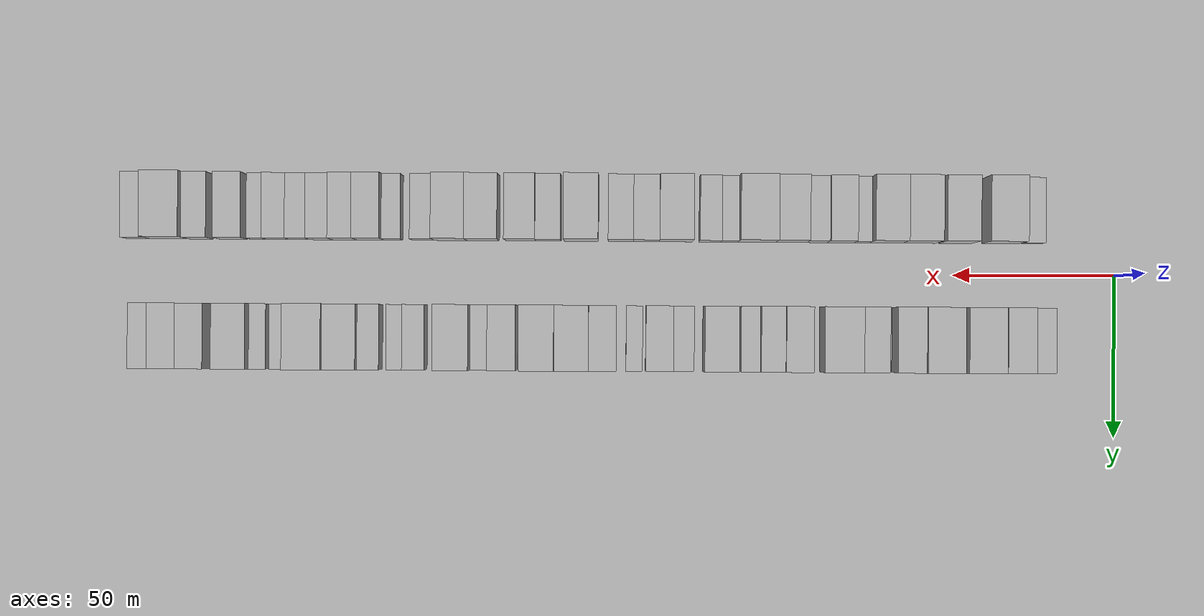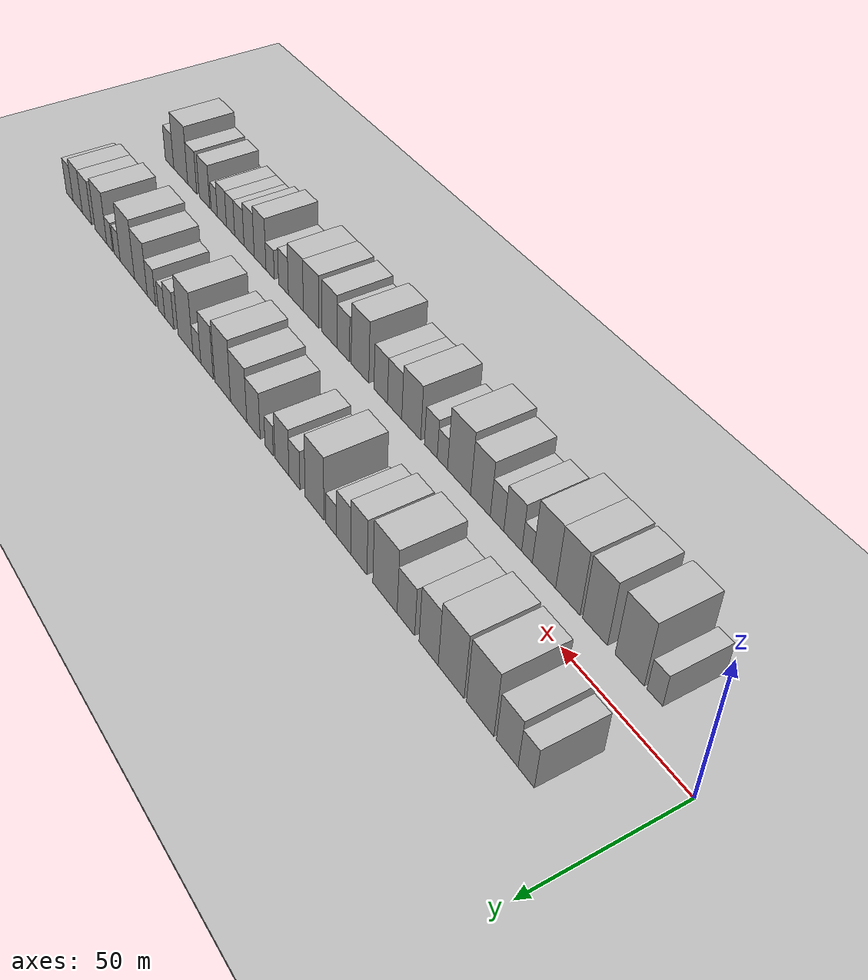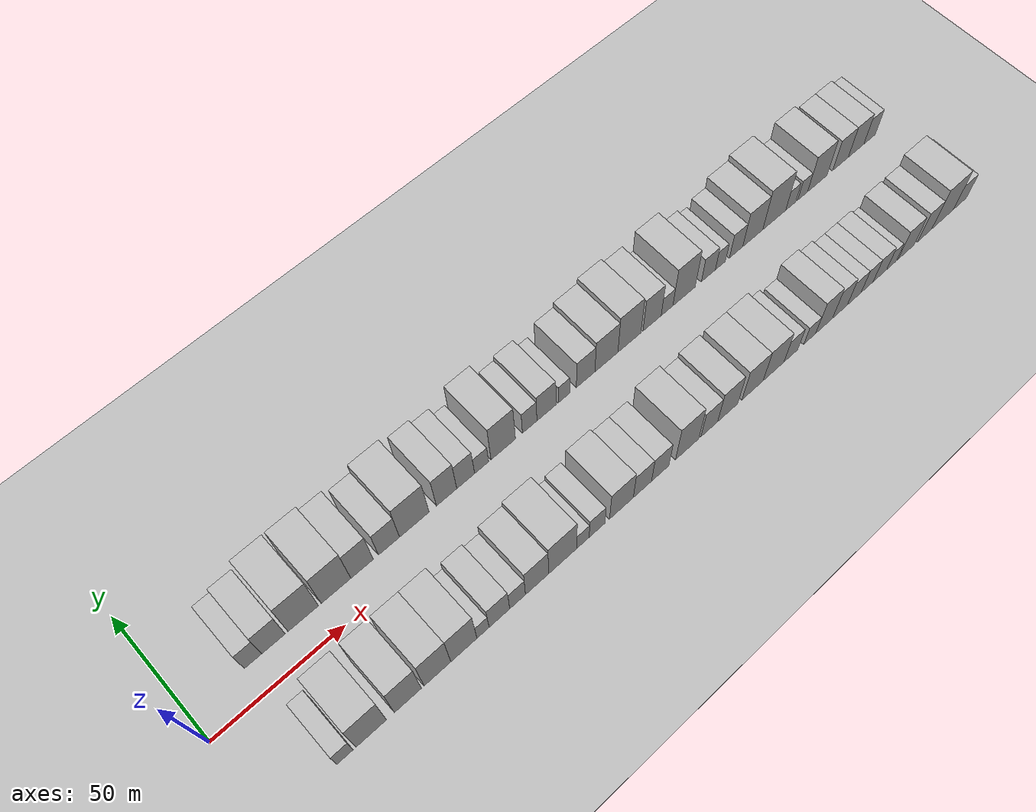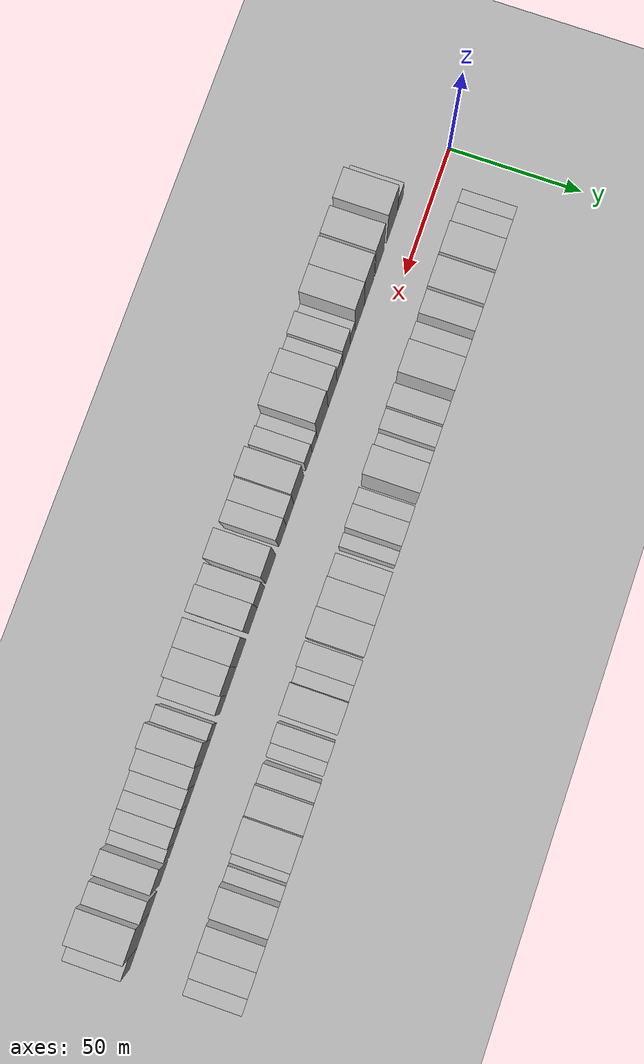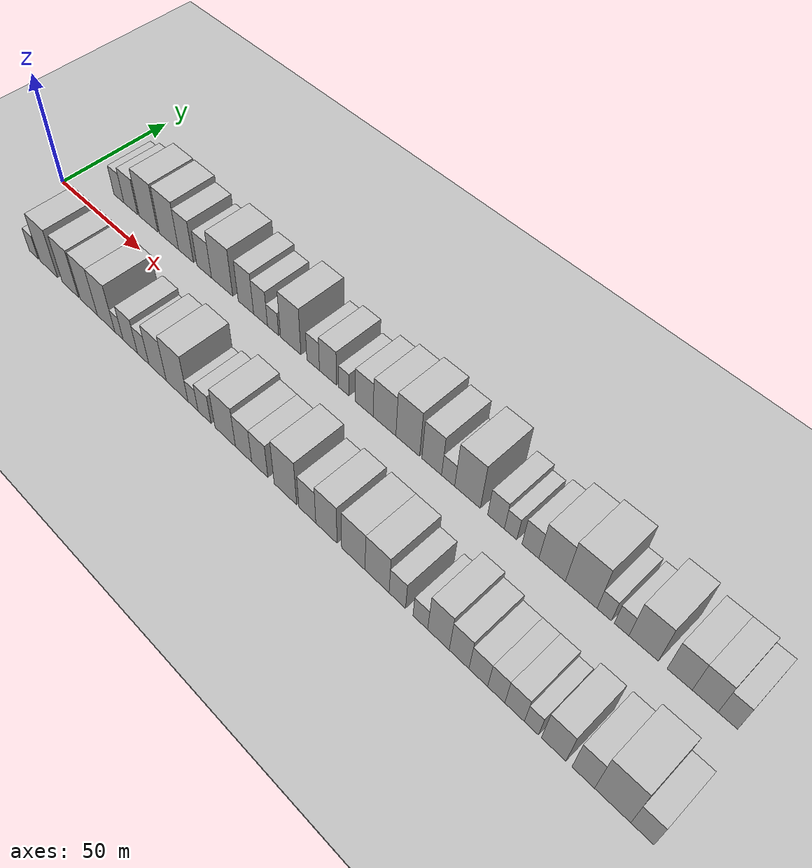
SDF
<?xml version="1.0" encoding="utf-8"?>

<sdf version="1.6">

   <world name="default">

      <gui fullscreen="0">

         <camera name="user_camera">

            <pose>-15 0 4.57585 0 0 0</pose>

            <view_controller>orbit</view_controller>

         </camera>

      </gui>

      <scene>

         <sky>

           <clouds>

             <speed>12</speed>

           </clouds>

         </sky>

         <ambient>0.4 0.4 0.4 1</ambient>

         <background>0.7 0.7 0.7 1</background>

         <shadows>1</shadows>

      </scene>

      <gravity>0 0 -9.8066</gravity>

      <magnetic_field>6e-06 2.3e-05 -4.2e-05</magnetic_field>

      <physics default="0" name="default_physics" type="ode">

         <ode>

            <solver>

               <type>quick</type>

               <iters>10</iters>

               <sor>1.0</sor>

               <use_dynamic_moi_rescaling>0</use_dynamic_moi_rescaling>

            </solver>

            <constraints>

               <cfm>0</cfm>

               <erp>0.2</erp>

               <contact_max_correcting_vel>100</contact_max_correcting_vel>

               <contact_surface_layer>0.001</contact_surface_layer>

            </constraints>

         </ode>

         <max_step_size>0.004</max_step_size>

         <real_time_factor>1</real_time_factor>

         <real_time_update_rate>250</real_time_update_rate>

      </physics>

      <light name="sun" type="directional">

         <cast_shadows>1</cast_shadows>

         <pose>0 0 10 0 0 0</pose>

         <diffuse>0.8 0.8 0.8 1</diffuse>

         <specular>0.2 0.2 0.2 1</specular>

         <attenuation>

            <range>1000</range>

            <constant>0.9</constant>

            <linear>0.01</linear>

            <quadratic>0.001</quadratic>

         </attenuation>

         <direction>-0.5 0.1 -0.9</direction>

      </light>

      <include>

         <name>ground_plane_1</name>

         <uri>model://HANNAS_ground_plane</uri>

         <pose>0 0 0  0 0 0</pose>

      </include>

      <include>

         <name>ground_plane_2</name>

         <uri>model://HANNAS_ground_plane</uri>

         <pose>100 0 0  0 0 0</pose>

      </include>

      <model name="building_1">

         <static>1</static>

         <pose frame="">23.1855 20.0000 0 0.000000 0.000000 1.570796</pose>

         <link name="link">

            <pose frame="">0 0 7.50 0 0 0</pose>

            <collision name="collision">

               <geometry>

                  <box>

                     <size>20.0000 6.3709 15.0000</size>

                  </box>

               </geometry>

               <max_contacts>10</max_contacts>

               <surface>

                  <contact>

                     <ode/>

                  </contact>

                  <bounce/>

                  <friction>

                     <torsional>

                        <ode/>

                     </torsional>

                     <ode/>

                  </friction>

               </surface>

            </collision>

            <visual name="visual">

               <cast_shadows>0</cast_shadows>

               <geometry>

                  <box>

                     <size>20.0000 6.3709 15.0000</size>

                  </box>

               </geometry>

               <material>

                  <script>

                     <uri>model://HANNAS_wall/materials/scripts</uri>

                     <uri>model://HANNAS_wall/materials/textures</uri>

                     <name>vrc/HANNAS_wall</name>

                  </script>

               </material>

            </visual>

            <self_collide>0</self_collide>

            <enable_wind>0</enable_wind>

            <kinematic>0</kinematic>

         </link>

      </model>

      <model name="building_2">

         <static>1</static>

         <pose frame="">30.7351 20.0000 0 0.000000 0.000000 1.570796</pose>

         <link name="link">

            <pose frame="">0 0 9.00 0 0 0</pose>

            <collision name="collision">

               <geometry>

                  <box>

                     <size>20.0000 8.7284 18.0000</size>

                  </box>

               </geometry>

               <max_contacts>10</max_contacts>

               <surface>

                  <contact>

                     <ode/>

                  </contact>

                  <bounce/>

                  <friction>

                     <torsional>

                        <ode/>

                     </torsional>

                     <ode/>

                  </friction>

               </surface>

            </collision>

            <visual name="visual">

               <cast_shadows>0</cast_shadows>

               <geometry>

                  <box>

                     <size>20.0000 8.7284 18.0000</size>

                  </box>

               </geometry>

               <material>

                  <script>

                     <uri>model://HANNAS_wall/materials/scripts</uri>

                     <uri>model://HANNAS_wall/materials/textures</uri>

                     <name>vrc/HANNAS_wall</name>

                  </script>

               </material>

            </visual>

            <self_collide>0</self_collide>

            <enable_wind>0</enable_wind>

            <kinematic>0</kinematic>

         </link>

      </model>

      <model name="building_3">

         <static>1</static>

         <pose frame="">41.8716 20.0000 0 0.000000 0.000000 1.570796</pose>

         <link name="link">

            <pose frame="">0 0 12.00 0 0 0</pose>

            <collision name="collision">

               <geometry>

                  <box>

                     <size>20.0000 11.5447 24.0000</size>

                  </box>

               </geometry>

               <max_contacts>10</max_contacts>

               <surface>

                  <contact>

                     <ode/>

                  </contact>

                  <bounce/>

                  <friction>

                     <torsional>

                        <ode/>

                     </torsional>

                     <ode/>

                  </friction>

               </surface>

            </collision>

            <visual name="visual">

               <cast_shadows>0</cast_shadows>

               <geometry>

                  <box>

                     <size>20.0000 11.5447 24.0000</size>

                  </box>

               </geometry>

               <material>

                  <script>

                     <uri>model://HANNAS_wall/materials/scripts</uri>

                     <uri>model://HANNAS_wall/materials/textures</uri>

                     <name>vrc/HANNAS_wall</name>

                  </script>

               </material>

            </visual>

            <self_collide>0</self_collide>

            <enable_wind>0</enable_wind>

            <kinematic>0</kinematic>

         </link>

      </model>

      <model name="building_4">

         <static>1</static>

         <pose frame="">54.3600 20.0000 0 0.000000 0.000000 1.570796</pose>

         <link name="link">

            <pose frame="">0 0 12.00 0 0 0</pose>

            <collision name="collision">

               <geometry>

                  <box>

                     <size>20.0000 11.4320 24.0000</size>

                  </box>

               </geometry>

               <max_contacts>10</max_contacts>

               <surface>

                  <contact>

                     <ode/>

                  </contact>

                  <bounce/>

                  <friction>

                     <torsional>

                        <ode/>

                     </torsional>

                     <ode/>

                  </friction>

               </surface>

            </collision>

            <visual name="visual">

               <cast_shadows>0</cast_shadows>

               <geometry>

                  <box>

                     <size>20.0000 11.4320 24.0000</size>

                  </box>

               </geometry>

               <material>

                  <script>

                     <uri>model://HANNAS_wall/materials/scripts</uri>

                     <uri>model://HANNAS_wall/materials/textures</uri>

                     <name>vrc/HANNAS_wall</name>

                  </script>

               </material>

            </visual>

            <self_collide>0</self_collide>

            <enable_wind>0</enable_wind>

            <kinematic>0</kinematic>

         </link>

      </model>

      <model name="building_5">

         <static>1</static>

         <pose frame="">64.4766 20.0000 0 0.000000 0.000000 1.570796</pose>

         <link name="link">

            <pose frame="">0 0 10.50 0 0 0</pose>

            <collision name="collision">

               <geometry>

                  <box>

                     <size>20.0000 8.8012 21.0000</size>

                  </box>

               </geometry>

               <max_contacts>10</max_contacts>

               <surface>

                  <contact>

                     <ode/>

                  </contact>

                  <bounce/>

                  <friction>

                     <torsional>

                        <ode/>

                     </torsional>

                     <ode/>

                  </friction>

               </surface>

            </collision>

            <visual name="visual">

               <cast_shadows>0</cast_shadows>

               <geometry>

                  <box>

                     <size>20.0000 8.8012 21.0000</size>

                  </box>

               </geometry>

               <material>

                  <script>

                     <uri>model://HANNAS_wall/materials/scripts</uri>

                     <uri>model://HANNAS_wall/materials/textures</uri>

                     <name>vrc/HANNAS_wall</name>

                  </script>

               </material>

            </visual>

            <self_collide>0</self_collide>

            <enable_wind>0</enable_wind>

            <kinematic>0</kinematic>

         </link>

      </model>

      <model name="building_6">

         <static>1</static>

         <pose frame="">75.0676 20.0000 0 0.000000 0.000000 1.570796</pose>

         <link name="link">

            <pose frame="">0 0 9.00 0 0 0</pose>

            <collision name="collision">

               <geometry>

                  <box>

                     <size>20.0000 8.3809 18.0000</size>

                  </box>

               </geometry>

               <max_contacts>10</max_contacts>

               <surface>

                  <contact>

                     <ode/>

                  </contact>

                  <bounce/>

                  <friction>

                     <torsional>

                        <ode/>

                     </torsional>

                     <ode/>

                  </friction>

               </surface>

            </collision>

            <visual name="visual">

               <cast_shadows>0</cast_shadows>

               <geometry>

                  <box>

                     <size>20.0000 8.3809 18.0000</size>

                  </box>

               </geometry>

               <material>

                  <script>

                     <uri>model://HANNAS_wall/materials/scripts</uri>

                     <uri>model://HANNAS_wall/materials/textures</uri>

                     <name>vrc/HANNAS_wall</name>

                  </script>

               </material>

            </visual>

            <self_collide>0</self_collide>

            <enable_wind>0</enable_wind>

            <kinematic>0</kinematic>

         </link>

      </model>

      <model name="building_7">

         <static>1</static>

         <pose frame="">85.2413 20.0000 0 0.000000 0.000000 1.570796</pose>

         <link name="link">

            <pose frame="">0 0 12.00 0 0 0</pose>

            <collision name="collision">

               <geometry>

                  <box>

                     <size>20.0000 11.9665 24.0000</size>

                  </box>

               </geometry>

               <max_contacts>10</max_contacts>

               <surface>

                  <contact>

                     <ode/>

                  </contact>

                  <bounce/>

                  <friction>

                     <torsional>

                        <ode/>

                     </torsional>

                     <ode/>

                  </friction>

               </surface>

            </collision>

            <visual name="visual">

               <cast_shadows>0</cast_shadows>

               <geometry>

                  <box>

                     <size>20.0000 11.9665 24.0000</size>

                  </box>

               </geometry>

               <material>

                  <script>

                     <uri>model://HANNAS_wall/materials/scripts</uri>

                     <uri>model://HANNAS_wall/materials/textures</uri>

                     <name>vrc/HANNAS_wall</name>

                  </script>

               </material>

            </visual>

            <self_collide>0</self_collide>

            <enable_wind>0</enable_wind>

            <kinematic>0</kinematic>

         </link>

      </model>

      <model name="building_8">

         <static>1</static>

         <pose frame="">98.4299 20.0000 0 0.000000 0.000000 1.570796</pose>

         <link name="link">

            <pose frame="">0 0 10.50 0 0 0</pose>

            <collision name="collision">

               <geometry>

                  <box>

                     <size>20.0000 8.4107 21.0000</size>

                  </box>

               </geometry>

               <max_contacts>10</max_contacts>

               <surface>

                  <contact>

                     <ode/>

                  </contact>

                  <bounce/>

                  <friction>

                     <torsional>

                        <ode/>

                     </torsional>

                     <ode/>

                  </friction>

               </surface>

            </collision>

            <visual name="visual">

               <cast_shadows>0</cast_shadows>

               <geometry>

                  <box>

                     <size>20.0000 8.4107 21.0000</size>

                  </box>

               </geometry>

               <material>

                  <script>

                     <uri>model://HANNAS_wall/materials/scripts</uri>

                     <uri>model://HANNAS_wall/materials/textures</uri>

                     <name>vrc/HANNAS_wall</name>

                  </script>

               </material>

            </visual>

            <self_collide>0</self_collide>

            <enable_wind>0</enable_wind>

            <kinematic>0</kinematic>

         </link>

      </model>

      <model name="building_9">

         <static>1</static>

         <pose frame="">106.3608 20.0000 0 0.000000 0.000000 1.570796</pose>

         <link name="link">

            <pose frame="">0 0 9.00 0 0 0</pose>

            <collision name="collision">

               <geometry>

                  <box>

                     <size>20.0000 7.4511 18.0000</size>

                  </box>

               </geometry>

               <max_contacts>10</max_contacts>

               <surface>

                  <contact>

                     <ode/>

                  </contact>

                  <bounce/>

                  <friction>

                     <torsional>

                        <ode/>

                     </torsional>

                     <ode/>

                  </friction>

               </surface>

            </collision>

            <visual name="visual">

               <cast_shadows>0</cast_shadows>

               <geometry>

                  <box>

                     <size>20.0000 7.4511 18.0000</size>

                  </box>

               </geometry>

               <material>

                  <script>

                     <uri>model://HANNAS_wall/materials/scripts</uri>

                     <uri>model://HANNAS_wall/materials/textures</uri>

                     <name>vrc/HANNAS_wall</name>

                  </script>

               </material>

            </visual>

            <self_collide>0</self_collide>

            <enable_wind>0</enable_wind>

            <kinematic>0</kinematic>

         </link>

      </model>

      <model name="building_10">

         <static>1</static>

         <pose frame="">113.0277 20.0000 0 0.000000 0.000000 1.570796</pose>

         <link name="link">

            <pose frame="">0 0 6.00 0 0 0</pose>

            <collision name="collision">

               <geometry>

                  <box>

                     <size>20.0000 5.8827 12.0000</size>

                  </box>

               </geometry>

               <max_contacts>10</max_contacts>

               <surface>

                  <contact>

                     <ode/>

                  </contact>

                  <bounce/>

                  <friction>

                     <torsional>

                        <ode/>

                     </torsional>

                     <ode/>

                  </friction>

               </surface>

            </collision>

            <visual name="visual">

               <cast_shadows>0</cast_shadows>

               <geometry>

                  <box>

                     <size>20.0000 5.8827 12.0000</size>

                  </box>

               </geometry>

               <material>

                  <script>

                     <uri>model://HANNAS_wall/materials/scripts</uri>

                     <uri>model://HANNAS_wall/materials/textures</uri>

                     <name>vrc/HANNAS_wall</name>

                  </script>

               </material>

            </visual>

            <self_collide>0</self_collide>

            <enable_wind>0</enable_wind>

            <kinematic>0</kinematic>

         </link>

      </model>

      <model name="building_11">

         <static>1</static>

         <pose frame="">122.2108 20.0000 0 0.000000 0.000000 1.570796</pose>

         <link name="link">

            <pose frame="">0 0 12.00 0 0 0</pose>

            <collision name="collision">

               <geometry>

                  <box>

                     <size>20.0000 10.4834 24.0000</size>

                  </box>

               </geometry>

               <max_contacts>10</max_contacts>

               <surface>

                  <contact>

                     <ode/>

                  </contact>

                  <bounce/>

                  <friction>

                     <torsional>

                        <ode/>

                     </torsional>

                     <ode/>

                  </friction>

               </surface>

            </collision>

            <visual name="visual">

               <cast_shadows>0</cast_shadows>

               <geometry>

                  <box>

                     <size>20.0000 10.4834 24.0000</size>

                  </box>

               </geometry>

               <material>

                  <script>

                     <uri>model://HANNAS_wall/materials/scripts</uri>

                     <uri>model://HANNAS_wall/materials/textures</uri>

                     <name>vrc/HANNAS_wall</name>

                  </script>

               </material>

            </visual>

            <self_collide>0</self_collide>

            <enable_wind>0</enable_wind>

            <kinematic>0</kinematic>

         </link>

      </model>

      <model name="building_12">

         <static>1</static>

         <pose frame="">133.6189 20.0000 0 0.000000 0.000000 1.570796</pose>

         <link name="link">

            <pose frame="">0 0 7.50 0 0 0</pose>

            <collision name="collision">

               <geometry>

                  <box>

                     <size>20.0000 6.3327 15.0000</size>

                  </box>

               </geometry>

               <max_contacts>10</max_contacts>

               <surface>

                  <contact>

                     <ode/>

                  </contact>

                  <bounce/>

                  <friction>

                     <torsional>

                        <ode/>

                     </torsional>

                     <ode/>

                  </friction>

               </surface>

            </collision>

            <visual name="visual">

               <cast_shadows>0</cast_shadows>

               <geometry>

                  <box>

                     <size>20.0000 6.3327 15.0000</size>

                  </box>

               </geometry>

               <material>

                  <script>

                     <uri>model://HANNAS_wall/materials/scripts</uri>

                     <uri>model://HANNAS_wall/materials/textures</uri>

                     <name>vrc/HANNAS_wall</name>

                  </script>

               </material>

            </visual>

            <self_collide>0</self_collide>

            <enable_wind>0</enable_wind>

            <kinematic>0</kinematic>

         </link>

      </model>

      <model name="building_13">

         <static>1</static>

         <pose frame="">140.9818 20.0000 0 0.000000 0.000000 1.570796</pose>

         <link name="link">

            <pose frame="">0 0 9.00 0 0 0</pose>

            <collision name="collision">

               <geometry>

                  <box>

                     <size>20.0000 8.3931 18.0000</size>

                  </box>

               </geometry>

               <max_contacts>10</max_contacts>

               <surface>

                  <contact>

                     <ode/>

                  </contact>

                  <bounce/>

                  <friction>

                     <torsional>

                        <ode/>

                     </torsional>

                     <ode/>

                  </friction>

               </surface>

            </collision>

            <visual name="visual">

               <cast_shadows>0</cast_shadows>

               <geometry>

                  <box>

                     <size>20.0000 8.3931 18.0000</size>

                  </box>

               </geometry>

               <material>

                  <script>

                     <uri>model://HANNAS_wall/materials/scripts</uri>

                     <uri>model://HANNAS_wall/materials/textures</uri>

                     <name>vrc/HANNAS_wall</name>

                  </script>

               </material>

            </visual>

            <self_collide>0</self_collide>

            <enable_wind>0</enable_wind>

            <kinematic>0</kinematic>

         </link>

      </model>

      <model name="building_14">

         <static>1</static>

         <pose frame="">148.6953 20.0000 0 0.000000 0.000000 1.570796</pose>

         <link name="link">

            <pose frame="">0 0 6.00 0 0 0</pose>

            <collision name="collision">

               <geometry>

                  <box>

                     <size>20.0000 5.0339 12.0000</size>

                  </box>

               </geometry>

               <max_contacts>10</max_contacts>

               <surface>

                  <contact>

                     <ode/>

                  </contact>

                  <bounce/>

                  <friction>

                     <torsional>

                        <ode/>

                     </torsional>

                     <ode/>

                  </friction>

               </surface>

            </collision>

            <visual name="visual">

               <cast_shadows>0</cast_shadows>

               <geometry>

                  <box>

                     <size>20.0000 5.0339 12.0000</size>

                  </box>

               </geometry>

               <material>

                  <script>

                     <uri>model://HANNAS_wall/materials/scripts</uri>

                     <uri>model://HANNAS_wall/materials/textures</uri>

                     <name>vrc/HANNAS_wall</name>

                  </script>

               </material>

            </visual>

            <self_collide>0</self_collide>

            <enable_wind>0</enable_wind>

            <kinematic>0</kinematic>

         </link>

      </model>

      <model name="building_15">

         <static>1</static>

         <pose frame="">158.4189 20.0000 0 0.000000 0.000000 1.570796</pose>

         <link name="link">

            <pose frame="">0 0 9.00 0 0 0</pose>

            <collision name="collision">

               <geometry>

                  <box>

                     <size>20.0000 8.4132 18.0000</size>

                  </box>

               </geometry>

               <max_contacts>10</max_contacts>

               <surface>

                  <contact>

                     <ode/>

                  </contact>

                  <bounce/>

                  <friction>

                     <torsional>

                        <ode/>

                     </torsional>

                     <ode/>

                  </friction>

               </surface>

            </collision>

            <visual name="visual">

               <cast_shadows>0</cast_shadows>

               <geometry>

                  <box>

                     <size>20.0000 8.4132 18.0000</size>

                  </box>

               </geometry>

               <material>

                  <script>

                     <uri>model://HANNAS_wall/materials/scripts</uri>

                     <uri>model://HANNAS_wall/materials/textures</uri>

                     <name>vrc/HANNAS_wall</name>

                  </script>

               </material>

            </visual>

            <self_collide>0</self_collide>

            <enable_wind>0</enable_wind>

            <kinematic>0</kinematic>

         </link>

      </model>

      <model name="building_16">

         <static>1</static>

         <pose frame="">167.8705 20.0000 0 0.000000 0.000000 1.570796</pose>

         <link name="link">

            <pose frame="">0 0 10.50 0 0 0</pose>

            <collision name="collision">

               <geometry>

                  <box>

                     <size>20.0000 10.4900 21.0000</size>

                  </box>

               </geometry>

               <max_contacts>10</max_contacts>

               <surface>

                  <contact>

                     <ode/>

                  </contact>

                  <bounce/>

                  <friction>

                     <torsional>

                        <ode/>

                     </torsional>

                     <ode/>

                  </friction>

               </surface>

            </collision>

            <visual name="visual">

               <cast_shadows>0</cast_shadows>

               <geometry>

                  <box>

                     <size>20.0000 10.4900 21.0000</size>

                  </box>

               </geometry>

               <material>

                  <script>

                     <uri>model://HANNAS_wall/materials/scripts</uri>

                     <uri>model://HANNAS_wall/materials/textures</uri>

                     <name>vrc/HANNAS_wall</name>

                  </script>

               </material>

            </visual>

            <self_collide>0</self_collide>

            <enable_wind>0</enable_wind>

            <kinematic>0</kinematic>

         </link>

      </model>

      <model name="building_17">

         <static>1</static>

         <pose frame="">178.4497 20.0000 0 0.000000 0.000000 1.570796</pose>

         <link name="link">

            <pose frame="">0 0 12.00 0 0 0</pose>

            <collision name="collision">

               <geometry>

                  <box>

                     <size>20.0000 10.6684 24.0000</size>

                  </box>

               </geometry>

               <max_contacts>10</max_contacts>

               <surface>

                  <contact>

                     <ode/>

                  </contact>

                  <bounce/>

                  <friction>

                     <torsional>

                        <ode/>

                     </torsional>

                     <ode/>

                  </friction>

               </surface>

            </collision>

            <visual name="visual">

               <cast_shadows>0</cast_shadows>

               <geometry>

                  <box>

                     <size>20.0000 10.6684 24.0000</size>

                  </box>

               </geometry>

               <material>

                  <script>

                     <uri>model://HANNAS_wall/materials/scripts</uri>

                     <uri>model://HANNAS_wall/materials/textures</uri>

                     <name>vrc/HANNAS_wall</name>

                  </script>

               </material>

            </visual>

            <self_collide>0</self_collide>

            <enable_wind>0</enable_wind>

            <kinematic>0</kinematic>

         </link>

      </model>

      <model name="building_18">

         <static>1</static>

         <pose frame="">189.0819 20.0000 0 0.000000 0.000000 1.570796</pose>

         <link name="link">

            <pose frame="">0 0 10.50 0 0 0</pose>

            <collision name="collision">

               <geometry>

                  <box>

                     <size>20.0000 8.5960 21.0000</size>

                  </box>

               </geometry>

               <max_contacts>10</max_contacts>

               <surface>

                  <contact>

                     <ode/>

                  </contact>

                  <bounce/>

                  <friction>

                     <torsional>

                        <ode/>

                     </torsional>

                     <ode/>

                  </friction>

               </surface>

            </collision>

            <visual name="visual">

               <cast_shadows>0</cast_shadows>

               <geometry>

                  <box>

                     <size>20.0000 8.5960 21.0000</size>

                  </box>

               </geometry>

               <material>

                  <script>

                     <uri>model://HANNAS_wall/materials/scripts</uri>

                     <uri>model://HANNAS_wall/materials/textures</uri>

                     <name>vrc/HANNAS_wall</name>

                  </script>

               </material>

            </visual>

            <self_collide>0</self_collide>

            <enable_wind>0</enable_wind>

            <kinematic>0</kinematic>

         </link>

      </model>

      <model name="building_19">

         <static>1</static>

         <pose frame="">196.1919 20.0000 0 0.000000 0.000000 1.570796</pose>

         <link name="link">

            <pose frame="">0 0 6.00 0 0 0</pose>

            <collision name="collision">

               <geometry>

                  <box>

                     <size>20.0000 5.6239 12.0000</size>

                  </box>

               </geometry>

               <max_contacts>10</max_contacts>

               <surface>

                  <contact>

                     <ode/>

                  </contact>

                  <bounce/>

                  <friction>

                     <torsional>

                        <ode/>

                     </torsional>

                     <ode/>

                  </friction>

               </surface>

            </collision>

            <visual name="visual">

               <cast_shadows>0</cast_shadows>

               <geometry>

                  <box>

                     <size>20.0000 5.6239 12.0000</size>

                  </box>

               </geometry>

               <material>

                  <script>

                     <uri>model://HANNAS_wall/materials/scripts</uri>

                     <uri>model://HANNAS_wall/materials/textures</uri>

                     <name>vrc/HANNAS_wall</name>

                  </script>

               </material>

            </visual>

            <self_collide>0</self_collide>

            <enable_wind>0</enable_wind>

            <kinematic>0</kinematic>

         </link>

      </model>

      <model name="building_20">

         <static>1</static>

         <pose frame="">204.3961 20.0000 0 0.000000 0.000000 1.570796</pose>

         <link name="link">

            <pose frame="">0 0 12.00 0 0 0</pose>

            <collision name="collision">

               <geometry>

                  <box>

                     <size>20.0000 10.7846 24.0000</size>

                  </box>

               </geometry>

               <max_contacts>10</max_contacts>

               <surface>

                  <contact>

                     <ode/>

                  </contact>

                  <bounce/>

                  <friction>

                     <torsional>

                        <ode/>

                     </torsional>

                     <ode/>

                  </friction>

               </surface>

            </collision>

            <visual name="visual">

               <cast_shadows>0</cast_shadows>

               <geometry>

                  <box>

                     <size>20.0000 10.7846 24.0000</size>

                  </box>

               </geometry>

               <material>

                  <script>

                     <uri>model://HANNAS_wall/materials/scripts</uri>

                     <uri>model://HANNAS_wall/materials/textures</uri>

                     <name>vrc/HANNAS_wall</name>

                  </script>

               </material>

            </visual>

            <self_collide>0</self_collide>

            <enable_wind>0</enable_wind>

            <kinematic>0</kinematic>

         </link>

      </model>

      <model name="building_21">

         <static>1</static>

         <pose frame="">216.2047 20.0000 0 0.000000 0.000000 1.570796</pose>

         <link name="link">

            <pose frame="">0 0 7.50 0 0 0</pose>

            <collision name="collision">

               <geometry>

                  <box>

                     <size>20.0000 6.8326 15.0000</size>

                  </box>

               </geometry>

               <max_contacts>10</max_contacts>

               <surface>

                  <contact>

                     <ode/>

                  </contact>

                  <bounce/>

                  <friction>

                     <torsional>

                        <ode/>

                     </torsional>

                     <ode/>

                  </friction>

               </surface>

            </collision>

            <visual name="visual">

               <cast_shadows>0</cast_shadows>

               <geometry>

                  <box>

                     <size>20.0000 6.8326 15.0000</size>

                  </box>

               </geometry>

               <material>

                  <script>

                     <uri>model://HANNAS_wall/materials/scripts</uri>

                     <uri>model://HANNAS_wall/materials/textures</uri>

                     <name>vrc/HANNAS_wall</name>

                  </script>

               </material>

            </visual>

            <self_collide>0</self_collide>

            <enable_wind>0</enable_wind>

            <kinematic>0</kinematic>

         </link>

      </model>

      <model name="building_22">

         <static>1</static>

         <pose frame="">222.1223 20.0000 0 0.000000 0.000000 1.570796</pose>

         <link name="link">

            <pose frame="">0 0 6.00 0 0 0</pose>

            <collision name="collision">

               <geometry>

                  <box>

                     <size>20.0000 5.0026 12.0000</size>

                  </box>

               </geometry>

               <max_contacts>10</max_contacts>

               <surface>

                  <contact>

                     <ode/>

                  </contact>

                  <bounce/>

                  <friction>

                     <torsional>

                        <ode/>

                     </torsional>

                     <ode/>

                  </friction>

               </surface>

            </collision>

            <visual name="visual">

               <cast_shadows>0</cast_shadows>

               <geometry>

                  <box>

                     <size>20.0000 5.0026 12.0000</size>

                  </box>

               </geometry>

               <material>

                  <script>

                     <uri>model://HANNAS_wall/materials/scripts</uri>

                     <uri>model://HANNAS_wall/materials/textures</uri>

                     <name>vrc/HANNAS_wall</name>

                  </script>

               </material>

            </visual>

            <self_collide>0</self_collide>

            <enable_wind>0</enable_wind>

            <kinematic>0</kinematic>

         </link>

      </model>

      <model name="building_23">

         <static>1</static>

         <pose frame="">229.9426 20.0000 0 0.000000 0.000000 1.570796</pose>

         <link name="link">

            <pose frame="">0 0 7.50 0 0 0</pose>

            <collision name="collision">

               <geometry>

                  <box>

                     <size>20.0000 6.6379 15.0000</size>

                  </box>

               </geometry>

               <max_contacts>10</max_contacts>

               <surface>

                  <contact>

                     <ode/>

                  </contact>

                  <bounce/>

                  <friction>

                     <torsional>

                        <ode/>

                     </torsional>

                     <ode/>

                  </friction>

               </surface>

            </collision>

            <visual name="visual">

               <cast_shadows>0</cast_shadows>

               <geometry>

                  <box>

                     <size>20.0000 6.6379 15.0000</size>

                  </box>

               </geometry>

               <material>

                  <script>

                     <uri>model://HANNAS_wall/materials/scripts</uri>

                     <uri>model://HANNAS_wall/materials/textures</uri>

                     <name>vrc/HANNAS_wall</name>

                  </script>

               </material>

            </visual>

            <self_collide>0</self_collide>

            <enable_wind>0</enable_wind>

            <kinematic>0</kinematic>

         </link>

      </model>

      <model name="building_24">

         <static>1</static>

         <pose frame="">238.3424 20.0000 0 0.000000 0.000000 1.570796</pose>

         <link name="link">

            <pose frame="">0 0 10.50 0 0 0</pose>

            <collision name="collision">

               <geometry>

                  <box>

                     <size>20.0000 10.1618 21.0000</size>

                  </box>

               </geometry>

               <max_contacts>10</max_contacts>

               <surface>

                  <contact>

                     <ode/>

                  </contact>

                  <bounce/>

                  <friction>

                     <torsional>

                        <ode/>

                     </torsional>

                     <ode/>

                  </friction>

               </surface>

            </collision>

            <visual name="visual">

               <cast_shadows>0</cast_shadows>

               <geometry>

                  <box>

                     <size>20.0000 10.1618 21.0000</size>

                  </box>

               </geometry>

               <material>

                  <script>

                     <uri>model://HANNAS_wall/materials/scripts</uri>

                     <uri>model://HANNAS_wall/materials/textures</uri>

                     <name>vrc/HANNAS_wall</name>

                  </script>

               </material>

            </visual>

            <self_collide>0</self_collide>

            <enable_wind>0</enable_wind>

            <kinematic>0</kinematic>

         </link>

      </model>

      <model name="building_25">

         <static>1</static>

         <pose frame="">249.3324 20.0000 0 0.000000 0.000000 1.570796</pose>

         <link name="link">

            <pose frame="">0 0 12.00 0 0 0</pose>

            <collision name="collision">

               <geometry>

                  <box>

                     <size>20.0000 11.8182 24.0000</size>

                  </box>

               </geometry>

               <max_contacts>10</max_contacts>

               <surface>

                  <contact>

                     <ode/>

                  </contact>

                  <bounce/>

                  <friction>

                     <torsional>

                        <ode/>

                     </torsional>

                     <ode/>

                  </friction>

               </surface>

            </collision>

            <visual name="visual">

               <cast_shadows>0</cast_shadows>

               <geometry>

                  <box>

                     <size>20.0000 11.8182 24.0000</size>

                  </box>

               </geometry>

               <material>

                  <script>

                     <uri>model://HANNAS_wall/materials/scripts</uri>

                     <uri>model://HANNAS_wall/materials/textures</uri>

                     <name>vrc/HANNAS_wall</name>

                  </script>

               </material>

            </visual>

            <self_collide>0</self_collide>

            <enable_wind>0</enable_wind>

            <kinematic>0</kinematic>

         </link>

      </model>

      <model name="building_26">

         <static>1</static>

         <pose frame="">257.8431 20.0000 0 0.000000 0.000000 1.570796</pose>

         <link name="link">

            <pose frame="">0 0 6.00 0 0 0</pose>

            <collision name="collision">

               <geometry>

                  <box>

                     <size>20.0000 5.2031 12.0000</size>

                  </box>

               </geometry>

               <max_contacts>10</max_contacts>

               <surface>

                  <contact>

                     <ode/>

                  </contact>

                  <bounce/>

                  <friction>

                     <torsional>

                        <ode/>

                     </torsional>

                     <ode/>

                  </friction>

               </surface>

            </collision>

            <visual name="visual">

               <cast_shadows>0</cast_shadows>

               <geometry>

                  <box>

                     <size>20.0000 5.2031 12.0000</size>

                  </box>

               </geometry>

               <material>

                  <script>

                     <uri>model://HANNAS_wall/materials/scripts</uri>

                     <uri>model://HANNAS_wall/materials/textures</uri>

                     <name>vrc/HANNAS_wall</name>

                  </script>

               </material>

            </visual>

            <self_collide>0</self_collide>

            <enable_wind>0</enable_wind>

            <kinematic>0</kinematic>

         </link>

      </model>

      <model name="building_27">

         <static>1</static>

         <pose frame="">264.0387 20.0000 0 0.000000 0.000000 1.570796</pose>

         <link name="link">

            <pose frame="">0 0 6.00 0 0 0</pose>

            <collision name="collision">

               <geometry>

                  <box>

                     <size>20.0000 5.1881 12.0000</size>

                  </box>

               </geometry>

               <max_contacts>10</max_contacts>

               <surface>

                  <contact>

                     <ode/>

                  </contact>

                  <bounce/>

                  <friction>

                     <torsional>

                        <ode/>

                     </torsional>

                     <ode/>

                  </friction>

               </surface>

            </collision>

            <visual name="visual">

               <cast_shadows>0</cast_shadows>

               <geometry>

                  <box>

                     <size>20.0000 5.1881 12.0000</size>

                  </box>

               </geometry>

               <material>

                  <script>

                     <uri>model://HANNAS_wall/materials/scripts</uri>

                     <uri>model://HANNAS_wall/materials/textures</uri>

                     <name>vrc/HANNAS_wall</name>

                  </script>

               </material>

            </visual>

            <self_collide>0</self_collide>

            <enable_wind>0</enable_wind>

            <kinematic>0</kinematic>

         </link>

      </model>

      <model name="building_28">

         <static>1</static>

         <pose frame="">271.7900 20.0000 0 0.000000 0.000000 1.570796</pose>

         <link name="link">

            <pose frame="">0 0 10.50 0 0 0</pose>

            <collision name="collision">

               <geometry>

                  <box>

                     <size>20.0000 10.3144 21.0000</size>

                  </box>

               </geometry>

               <max_contacts>10</max_contacts>

               <surface>

                  <contact>

                     <ode/>

                  </contact>

                  <bounce/>

                  <friction>

                     <torsional>

                        <ode/>

                     </torsional>

                     <ode/>

                  </friction>

               </surface>

            </collision>

            <visual name="visual">

               <cast_shadows>0</cast_shadows>

               <geometry>

                  <box>

                     <size>20.0000 10.3144 21.0000</size>

                  </box>

               </geometry>

               <material>

                  <script>

                     <uri>model://HANNAS_wall/materials/scripts</uri>

                     <uri>model://HANNAS_wall/materials/textures</uri>

                     <name>vrc/HANNAS_wall</name>

                  </script>

               </material>

            </visual>

            <self_collide>0</self_collide>

            <enable_wind>0</enable_wind>

            <kinematic>0</kinematic>

         </link>

      </model>

      <model name="building_29">

         <static>1</static>

         <pose frame="">284.1666 20.0000 0 0.000000 0.000000 1.570796</pose>

         <link name="link">

            <pose frame="">0 0 9.00 0 0 0</pose>

            <collision name="collision">

               <geometry>

                  <box>

                     <size>20.0000 8.4388 18.0000</size>

                  </box>

               </geometry>

               <max_contacts>10</max_contacts>

               <surface>

                  <contact>

                     <ode/>

                  </contact>

                  <bounce/>

                  <friction>

                     <torsional>

                        <ode/>

                     </torsional>

                     <ode/>

                  </friction>

               </surface>

            </collision>

            <visual name="visual">

               <cast_shadows>0</cast_shadows>

               <geometry>

                  <box>

                     <size>20.0000 8.4388 18.0000</size>

                  </box>

               </geometry>

               <material>

                  <script>

                     <uri>model://HANNAS_wall/materials/scripts</uri>

                     <uri>model://HANNAS_wall/materials/textures</uri>

                     <name>vrc/HANNAS_wall</name>

                  </script>

               </material>

            </visual>

            <self_collide>0</self_collide>

            <enable_wind>0</enable_wind>

            <kinematic>0</kinematic>

         </link>

      </model>

      <model name="building_30">

         <static>1</static>

         <pose frame="">292.6248 20.0000 0 0.000000 0.000000 1.570796</pose>

         <link name="link">

            <pose frame="">0 0 9.00 0 0 0</pose>

            <collision name="collision">

               <geometry>

                  <box>

                     <size>20.0000 8.4776 18.0000</size>

                  </box>

               </geometry>

               <max_contacts>10</max_contacts>

               <surface>

                  <contact>

                     <ode/>

                  </contact>

                  <bounce/>

                  <friction>

                     <torsional>

                        <ode/>

                     </torsional>

                     <ode/>

                  </friction>

               </surface>

            </collision>

            <visual name="visual">

               <cast_shadows>0</cast_shadows>

               <geometry>

                  <box>

                     <size>20.0000 8.4776 18.0000</size>

                  </box>

               </geometry>

               <material>

                  <script>

                     <uri>model://HANNAS_wall/materials/scripts</uri>

                     <uri>model://HANNAS_wall/materials/textures</uri>

                     <name>vrc/HANNAS_wall</name>

                  </script>

               </material>

            </visual>

            <self_collide>0</self_collide>

            <enable_wind>0</enable_wind>

            <kinematic>0</kinematic>

         </link>

      </model>

      <model name="building_31">

         <static>1</static>

         <pose frame="">300.0310 20.0000 0 0.000000 0.000000 1.570796</pose>

         <link name="link">

            <pose frame="">0 0 7.50 0 0 0</pose>

            <collision name="collision">

               <geometry>

                  <box>

                     <size>20.0000 6.3350 15.0000</size>

                  </box>

               </geometry>

               <max_contacts>10</max_contacts>

               <surface>

                  <contact>

                     <ode/>

                  </contact>

                  <bounce/>

                  <friction>

                     <torsional>

                        <ode/>

                     </torsional>

                     <ode/>

                  </friction>

               </surface>

            </collision>

            <visual name="visual">

               <cast_shadows>0</cast_shadows>

               <geometry>

                  <box>

                     <size>20.0000 6.3350 15.0000</size>

                  </box>

               </geometry>

               <material>

                  <script>

                     <uri>model://HANNAS_wall/materials/scripts</uri>

                     <uri>model://HANNAS_wall/materials/textures</uri>

                     <name>vrc/HANNAS_wall</name>

                  </script>

               </material>

            </visual>

            <self_collide>0</self_collide>

            <enable_wind>0</enable_wind>

            <kinematic>0</kinematic>

         </link>

      </model>

      <model name="building_32">

         <static>1</static>

         <pose frame="">25.9461 -20.0000 0 0.000000 0.000000 1.570796</pose>

         <link name="link">

            <pose frame="">0 0 6.00 0 0 0</pose>

            <collision name="collision">

               <geometry>

                  <box>

                     <size>20.0000 5.8921 12.0000</size>

                  </box>

               </geometry>

               <max_contacts>10</max_contacts>

               <surface>

                  <contact>

                     <ode/>

                  </contact>

                  <bounce/>

                  <friction>

                     <torsional>

                        <ode/>

                     </torsional>

                     <ode/>

                  </friction>

               </surface>

            </collision>

            <visual name="visual">

               <cast_shadows>0</cast_shadows>

               <geometry>

                  <box>

                     <size>20.0000 5.8921 12.0000</size>

                  </box>

               </geometry>

               <material>

                  <script>

                     <uri>model://HANNAS_wall/materials/scripts</uri>

                     <uri>model://HANNAS_wall/materials/textures</uri>

                     <name>vrc/HANNAS_wall</name>

                  </script>

               </material>

            </visual>

            <self_collide>0</self_collide>

            <enable_wind>0</enable_wind>

            <kinematic>0</kinematic>

         </link>

      </model>

      <model name="building_33">

         <static>1</static>

         <pose frame="">35.5581 -20.0000 0 0.000000 0.000000 1.570796</pose>

         <link name="link">

            <pose frame="">0 0 12.00 0 0 0</pose>

            <collision name="collision">

               <geometry>

                  <box>

                     <size>20.0000 11.3319 24.0000</size>

                  </box>

               </geometry>

               <max_contacts>10</max_contacts>

               <surface>

                  <contact>

                     <ode/>

                  </contact>

                  <bounce/>

                  <friction>

                     <torsional>

                        <ode/>

                     </torsional>

                     <ode/>

                  </friction>

               </surface>

            </collision>

            <visual name="visual">

               <cast_shadows>0</cast_shadows>

               <geometry>

                  <box>

                     <size>20.0000 11.3319 24.0000</size>

                  </box>

               </geometry>

               <material>

                  <script>

                     <uri>model://HANNAS_wall/materials/scripts</uri>

                     <uri>model://HANNAS_wall/materials/textures</uri>

                     <name>vrc/HANNAS_wall</name>

                  </script>

               </material>

            </visual>

            <self_collide>0</self_collide>

            <enable_wind>0</enable_wind>

            <kinematic>0</kinematic>

         </link>

      </model>

      <model name="building_34">

         <static>1</static>

         <pose frame="">49.3231 -20.0000 0 0.000000 0.000000 1.570796</pose>

         <link name="link">

            <pose frame="">0 0 12.00 0 0 0</pose>

            <collision name="collision">

               <geometry>

                  <box>

                     <size>20.0000 10.1981 24.0000</size>

                  </box>

               </geometry>

               <max_contacts>10</max_contacts>

               <surface>

                  <contact>

                     <ode/>

                  </contact>

                  <bounce/>

                  <friction>

                     <torsional>

                        <ode/>

                     </torsional>

                     <ode/>

                  </friction>

               </surface>

            </collision>

            <visual name="visual">

               <cast_shadows>0</cast_shadows>

               <geometry>

                  <box>

                     <size>20.0000 10.1981 24.0000</size>

                  </box>

               </geometry>

               <material>

                  <script>

                     <uri>model://HANNAS_wall/materials/scripts</uri>

                     <uri>model://HANNAS_wall/materials/textures</uri>

                     <name>vrc/HANNAS_wall</name>

                  </script>

               </material>

            </visual>

            <self_collide>0</self_collide>

            <enable_wind>0</enable_wind>

            <kinematic>0</kinematic>

         </link>

      </model>

      <model name="building_35">

         <static>1</static>

         <pose frame="">60.6073 -20.0000 0 0.000000 0.000000 1.570796</pose>

         <link name="link">

            <pose frame="">0 0 12.00 0 0 0</pose>

            <collision name="collision">

               <geometry>

                  <box>

                     <size>20.0000 10.3703 24.0000</size>

                  </box>

               </geometry>

               <max_contacts>10</max_contacts>

               <surface>

                  <contact>

                     <ode/>

                  </contact>

                  <bounce/>

                  <friction>

                     <torsional>

                        <ode/>

                     </torsional>

                     <ode/>

                  </friction>

               </surface>

            </collision>

            <visual name="visual">

               <cast_shadows>0</cast_shadows>

               <geometry>

                  <box>

                     <size>20.0000 10.3703 24.0000</size>

                  </box>

               </geometry>

               <material>

                  <script>

                     <uri>model://HANNAS_wall/materials/scripts</uri>

                     <uri>model://HANNAS_wall/materials/textures</uri>

                     <name>vrc/HANNAS_wall</name>

                  </script>

               </material>

            </visual>

            <self_collide>0</self_collide>

            <enable_wind>0</enable_wind>

            <kinematic>0</kinematic>

         </link>

      </model>

      <model name="building_36">

         <static>1</static>

         <pose frame="">70.9142 -20.0000 0 0.000000 0.000000 1.570796</pose>

         <link name="link">

            <pose frame="">0 0 12.00 0 0 0</pose>

            <collision name="collision">

               <geometry>

                  <box>

                     <size>20.0000 10.2434 24.0000</size>

                  </box>

               </geometry>

               <max_contacts>10</max_contacts>

               <surface>

                  <contact>

                     <ode/>

                  </contact>

                  <bounce/>

                  <friction>

                     <torsional>

                        <ode/>

                     </torsional>

                     <ode/>

                  </friction>

               </surface>

            </collision>

            <visual name="visual">

               <cast_shadows>0</cast_shadows>

               <geometry>

                  <box>

                     <size>20.0000 10.2434 24.0000</size>

                  </box>

               </geometry>

               <material>

                  <script>

                     <uri>model://HANNAS_wall/materials/scripts</uri>

                     <uri>model://HANNAS_wall/materials/textures</uri>

                     <name>vrc/HANNAS_wall</name>

                  </script>

               </material>

            </visual>

            <self_collide>0</self_collide>

            <enable_wind>0</enable_wind>

            <kinematic>0</kinematic>

         </link>

      </model>

      <model name="building_37">

         <static>1</static>

         <pose frame="">78.4433 -20.0000 0 0.000000 0.000000 1.570796</pose>

         <link name="link">

            <pose frame="">0 0 6.00 0 0 0</pose>

            <collision name="collision">

               <geometry>

                  <box>

                     <size>20.0000 4.8148 12.0000</size>

                  </box>

               </geometry>

               <max_contacts>10</max_contacts>

               <surface>

                  <contact>

                     <ode/>

                  </contact>

                  <bounce/>

                  <friction>

                     <torsional>

                        <ode/>

                     </torsional>

                     <ode/>

                  </friction>

               </surface>

            </collision>

            <visual name="visual">

               <cast_shadows>0</cast_shadows>

               <geometry>

                  <box>

                     <size>20.0000 4.8148 12.0000</size>

                  </box>

               </geometry>

               <material>

                  <script>

                     <uri>model://HANNAS_wall/materials/scripts</uri>

                     <uri>model://HANNAS_wall/materials/textures</uri>

                     <name>vrc/HANNAS_wall</name>

                  </script>

               </material>

            </visual>

            <self_collide>0</self_collide>

            <enable_wind>0</enable_wind>

            <kinematic>0</kinematic>

         </link>

      </model>

      <model name="building_38">

         <static>1</static>

         <pose frame="">84.9782 -20.0000 0 0.000000 0.000000 1.570796</pose>

         <link name="link">

            <pose frame="">0 0 9.00 0 0 0</pose>

            <collision name="collision">

               <geometry>

                  <box>

                     <size>20.0000 8.2550 18.0000</size>

                  </box>

               </geometry>

               <max_contacts>10</max_contacts>

               <surface>

                  <contact>

                     <ode/>

                  </contact>

                  <bounce/>

                  <friction>

                     <torsional>

                        <ode/>

                     </torsional>

                     <ode/>

                  </friction>

               </surface>

            </collision>

            <visual name="visual">

               <cast_shadows>0</cast_shadows>

               <geometry>

                  <box>

                     <size>20.0000 8.2550 18.0000</size>

                  </box>

               </geometry>

               <material>

                  <script>

                     <uri>model://HANNAS_wall/materials/scripts</uri>

                     <uri>model://HANNAS_wall/materials/textures</uri>

                     <name>vrc/HANNAS_wall</name>

                  </script>

               </material>

            </visual>

            <self_collide>0</self_collide>

            <enable_wind>0</enable_wind>

            <kinematic>0</kinematic>

         </link>

      </model>

      <model name="building_39">

         <static>1</static>

         <pose frame="">92.3051 -20.0000 0 0.000000 0.000000 1.570796</pose>

         <link name="link">

            <pose frame="">0 0 7.50 0 0 0</pose>

            <collision name="collision">

               <geometry>

                  <box>

                     <size>20.0000 6.3988 15.0000</size>

                  </box>

               </geometry>

               <max_contacts>10</max_contacts>

               <surface>

                  <contact>

                     <ode/>

                  </contact>

                  <bounce/>

                  <friction>

                     <torsional>

                        <ode/>

                     </torsional>

                     <ode/>

                  </friction>

               </surface>

            </collision>

            <visual name="visual">

               <cast_shadows>0</cast_shadows>

               <geometry>

                  <box>

                     <size>20.0000 6.3988 15.0000</size>

                  </box>

               </geometry>

               <material>

                  <script>

                     <uri>model://HANNAS_wall/materials/scripts</uri>

                     <uri>model://HANNAS_wall/materials/textures</uri>

                     <name>vrc/HANNAS_wall</name>

                  </script>

               </material>

            </visual>

            <self_collide>0</self_collide>

            <enable_wind>0</enable_wind>

            <kinematic>0</kinematic>

         </link>

      </model>

      <model name="building_40">

         <static>1</static>

         <pose frame="">100.2814 -20.0000 0 0.000000 0.000000 1.570796</pose>

         <link name="link">

            <pose frame="">0 0 10.50 0 0 0</pose>

            <collision name="collision">

               <geometry>

                  <box>

                     <size>20.0000 9.5539 21.0000</size>

                  </box>

               </geometry>

               <max_contacts>10</max_contacts>

               <surface>

                  <contact>

                     <ode/>

                  </contact>

                  <bounce/>

                  <friction>

                     <torsional>

                        <ode/>

                     </torsional>

                     <ode/>

                  </friction>

               </surface>

            </collision>

            <visual name="visual">

               <cast_shadows>0</cast_shadows>

               <geometry>

                  <box>

                     <size>20.0000 9.5539 21.0000</size>

                  </box>

               </geometry>

               <material>

                  <script>

                     <uri>model://HANNAS_wall/materials/scripts</uri>

                     <uri>model://HANNAS_wall/materials/textures</uri>

                     <name>vrc/HANNAS_wall</name>

                  </script>

               </material>

            </visual>

            <self_collide>0</self_collide>

            <enable_wind>0</enable_wind>

            <kinematic>0</kinematic>

         </link>

      </model>

      <model name="building_41">

         <static>1</static>

         <pose frame="">110.8778 -20.0000 0 0.000000 0.000000 1.570796</pose>

         <link name="link">

            <pose frame="">0 0 12.00 0 0 0</pose>

            <collision name="collision">

               <geometry>

                  <box>

                     <size>20.0000 11.6388 24.0000</size>

                  </box>

               </geometry>

               <max_contacts>10</max_contacts>

               <surface>

                  <contact>

                     <ode/>

                  </contact>

                  <bounce/>

                  <friction>

                     <torsional>

                        <ode/>

                     </torsional>

                     <ode/>

                  </friction>

               </surface>

            </collision>

            <visual name="visual">

               <cast_shadows>0</cast_shadows>

               <geometry>

                  <box>

                     <size>20.0000 11.6388 24.0000</size>

                  </box>

               </geometry>

               <material>

                  <script>

                     <uri>model://HANNAS_wall/materials/scripts</uri>

                     <uri>model://HANNAS_wall/materials/textures</uri>

                     <name>vrc/HANNAS_wall</name>

                  </script>

               </material>

            </visual>

            <self_collide>0</self_collide>

            <enable_wind>0</enable_wind>

            <kinematic>0</kinematic>

         </link>

      </model>

      <model name="building_42">

         <static>1</static>

         <pose frame="">119.3610 -20.0000 0 0.000000 0.000000 1.570796</pose>

         <link name="link">

            <pose frame="">0 0 6.00 0 0 0</pose>

            <collision name="collision">

               <geometry>

                  <box>

                     <size>20.0000 5.3276 12.0000</size>

                  </box>

               </geometry>

               <max_contacts>10</max_contacts>

               <surface>

                  <contact>

                     <ode/>

                  </contact>

                  <bounce/>

                  <friction>

                     <torsional>

                        <ode/>

                     </torsional>

                     <ode/>

                  </friction>

               </surface>

            </collision>

            <visual name="visual">

               <cast_shadows>0</cast_shadows>

               <geometry>

                  <box>

                     <size>20.0000 5.3276 12.0000</size>

                  </box>

               </geometry>

               <material>

                  <script>

                     <uri>model://HANNAS_wall/materials/scripts</uri>

                     <uri>model://HANNAS_wall/materials/textures</uri>

                     <name>vrc/HANNAS_wall</name>

                  </script>

               </material>

            </visual>

            <self_collide>0</self_collide>

            <enable_wind>0</enable_wind>

            <kinematic>0</kinematic>

         </link>

      </model>

      <model name="building_43">

         <static>1</static>

         <pose frame="">125.3902 -20.0000 0 0.000000 0.000000 1.570796</pose>

         <link name="link">

            <pose frame="">0 0 7.50 0 0 0</pose>

            <collision name="collision">

               <geometry>

                  <box>

                     <size>20.0000 6.7308 15.0000</size>

                  </box>

               </geometry>

               <max_contacts>10</max_contacts>

               <surface>

                  <contact>

                     <ode/>

                  </contact>

                  <bounce/>

                  <friction>

                     <torsional>

                        <ode/>

                     </torsional>

                     <ode/>

                  </friction>

               </surface>

            </collision>

            <visual name="visual">

               <cast_shadows>0</cast_shadows>

               <geometry>

                  <box>

                     <size>20.0000 6.7308 15.0000</size>

                  </box>

               </geometry>

               <material>

                  <script>

                     <uri>model://HANNAS_wall/materials/scripts</uri>

                     <uri>model://HANNAS_wall/materials/textures</uri>

                     <name>vrc/HANNAS_wall</name>

                  </script>

               </material>

            </visual>

            <self_collide>0</self_collide>

            <enable_wind>0</enable_wind>

            <kinematic>0</kinematic>

         </link>

      </model>

      <model name="building_44">

         <static>1</static>

         <pose frame="">135.9270 -20.0000 0 0.000000 0.000000 1.570796</pose>

         <link name="link">

            <pose frame="">0 0 10.50 0 0 0</pose>

            <collision name="collision">

               <geometry>

                  <box>

                     <size>20.0000 10.3427 21.0000</size>

                  </box>

               </geometry>

               <max_contacts>10</max_contacts>

               <surface>

                  <contact>

                     <ode/>

                  </contact>

                  <bounce/>

                  <friction>

                     <torsional>

                        <ode/>

                     </torsional>

                     <ode/>

                  </friction>

               </surface>

            </collision>

            <visual name="visual">

               <cast_shadows>0</cast_shadows>

               <geometry>

                  <box>

                     <size>20.0000 10.3427 21.0000</size>

                  </box>

               </geometry>

               <material>

                  <script>

                     <uri>model://HANNAS_wall/materials/scripts</uri>

                     <uri>model://HANNAS_wall/materials/textures</uri>

                     <name>vrc/HANNAS_wall</name>

                  </script>

               </material>

            </visual>

            <self_collide>0</self_collide>

            <enable_wind>0</enable_wind>

            <kinematic>0</kinematic>

         </link>

      </model>

      <model name="building_45">

         <static>1</static>

         <pose frame="">145.1123 -20.0000 0 0.000000 0.000000 1.570796</pose>

         <link name="link">

            <pose frame="">0 0 9.00 0 0 0</pose>

            <collision name="collision">

               <geometry>

                  <box>

                     <size>20.0000 8.0279 18.0000</size>

                  </box>

               </geometry>

               <max_contacts>10</max_contacts>

               <surface>

                  <contact>

                     <ode/>

                  </contact>

                  <bounce/>

                  <friction>

                     <torsional>

                        <ode/>

                     </torsional>

                     <ode/>

                  </friction>

               </surface>

            </collision>

            <visual name="visual">

               <cast_shadows>0</cast_shadows>

               <geometry>

                  <box>

                     <size>20.0000 8.0279 18.0000</size>

                  </box>

               </geometry>

               <material>

                  <script>

                     <uri>model://HANNAS_wall/materials/scripts</uri>

                     <uri>model://HANNAS_wall/materials/textures</uri>

                     <name>vrc/HANNAS_wall</name>

                  </script>

               </material>

            </visual>

            <self_collide>0</self_collide>

            <enable_wind>0</enable_wind>

            <kinematic>0</kinematic>

         </link>

      </model>

      <model name="building_46">

         <static>1</static>

         <pose frame="">153.0049 -20.0000 0 0.000000 0.000000 1.570796</pose>

         <link name="link">

            <pose frame="">0 0 9.00 0 0 0</pose>

            <collision name="collision">

               <geometry>

                  <box>

                     <size>20.0000 7.7573 18.0000</size>

                  </box>

               </geometry>

               <max_contacts>10</max_contacts>

               <surface>

                  <contact>

                     <ode/>

                  </contact>

                  <bounce/>

                  <friction>

                     <torsional>

                        <ode/>

                     </torsional>

                     <ode/>

                  </friction>

               </surface>

            </collision>

            <visual name="visual">

               <cast_shadows>0</cast_shadows>

               <geometry>

                  <box>

                     <size>20.0000 7.7573 18.0000</size>

                  </box>

               </geometry>

               <material>

                  <script>

                     <uri>model://HANNAS_wall/materials/scripts</uri>

                     <uri>model://HANNAS_wall/materials/textures</uri>

                     <name>vrc/HANNAS_wall</name>

                  </script>

               </material>

            </visual>

            <self_collide>0</self_collide>

            <enable_wind>0</enable_wind>

            <kinematic>0</kinematic>

         </link>

      </model>

      <model name="building_47">

         <static>1</static>

         <pose frame="">165.1466 -20.0000 0 0.000000 0.000000 1.570796</pose>

         <link name="link">

            <pose frame="">0 0 12.00 0 0 0</pose>

            <collision name="collision">

               <geometry>

                  <box>

                     <size>20.0000 10.5262 24.0000</size>

                  </box>

               </geometry>

               <max_contacts>10</max_contacts>

               <surface>

                  <contact>

                     <ode/>

                  </contact>

                  <bounce/>

                  <friction>

                     <torsional>

                        <ode/>

                     </torsional>

                     <ode/>

                  </friction>

               </surface>

            </collision>

            <visual name="visual">

               <cast_shadows>0</cast_shadows>

               <geometry>

                  <box>

                     <size>20.0000 10.5262 24.0000</size>

                  </box>

               </geometry>

               <material>

                  <script>

                     <uri>model://HANNAS_wall/materials/scripts</uri>

                     <uri>model://HANNAS_wall/materials/textures</uri>

                     <name>vrc/HANNAS_wall</name>

                  </script>

               </material>

            </visual>

            <self_collide>0</self_collide>

            <enable_wind>0</enable_wind>

            <kinematic>0</kinematic>

         </link>

      </model>

      <model name="building_48">

         <static>1</static>

         <pose frame="">175.2684 -20.0000 0 0.000000 0.000000 1.570796</pose>

         <link name="link">

            <pose frame="">0 0 9.00 0 0 0</pose>

            <collision name="collision">

               <geometry>

                  <box>

                     <size>20.0000 7.7175 18.0000</size>

                  </box>

               </geometry>

               <max_contacts>10</max_contacts>

               <surface>

                  <contact>

                     <ode/>

                  </contact>

                  <bounce/>

                  <friction>

                     <torsional>

                        <ode/>

                     </torsional>

                     <ode/>

                  </friction>

               </surface>

            </collision>

            <visual name="visual">

               <cast_shadows>0</cast_shadows>

               <geometry>

                  <box>

                     <size>20.0000 7.7175 18.0000</size>

                  </box>

               </geometry>

               <material>

                  <script>

                     <uri>model://HANNAS_wall/materials/scripts</uri>

                     <uri>model://HANNAS_wall/materials/textures</uri>

                     <name>vrc/HANNAS_wall</name>

                  </script>

               </material>

            </visual>

            <self_collide>0</self_collide>

            <enable_wind>0</enable_wind>

            <kinematic>0</kinematic>

         </link>

      </model>

      <model name="building_49">

         <static>1</static>

         <pose frame="">183.8423 -20.0000 0 0.000000 0.000000 1.570796</pose>

         <link name="link">

            <pose frame="">0 0 10.50 0 0 0</pose>

            <collision name="collision">

               <geometry>

                  <box>

                     <size>20.0000 9.4302 21.0000</size>

                  </box>

               </geometry>

               <max_contacts>10</max_contacts>

               <surface>

                  <contact>

                     <ode/>

                  </contact>

                  <bounce/>

                  <friction>

                     <torsional>

                        <ode/>

                     </torsional>

                     <ode/>

                  </friction>

               </surface>

            </collision>

            <visual name="visual">

               <cast_shadows>0</cast_shadows>

               <geometry>

                  <box>

                     <size>20.0000 9.4302 21.0000</size>

                  </box>

               </geometry>

               <material>

                  <script>

                     <uri>model://HANNAS_wall/materials/scripts</uri>

                     <uri>model://HANNAS_wall/materials/textures</uri>

                     <name>vrc/HANNAS_wall</name>

                  </script>

               </material>

            </visual>

            <self_collide>0</self_collide>

            <enable_wind>0</enable_wind>

            <kinematic>0</kinematic>

         </link>

      </model>

      <model name="building_50">

         <static>1</static>

         <pose frame="">195.6039 -20.0000 0 0.000000 0.000000 1.570796</pose>

         <link name="link">

            <pose frame="">0 0 10.50 0 0 0</pose>

            <collision name="collision">

               <geometry>

                  <box>

                     <size>20.0000 10.0931 21.0000</size>

                  </box>

               </geometry>

               <max_contacts>10</max_contacts>

               <surface>

                  <contact>

                     <ode/>

                  </contact>

                  <bounce/>

                  <friction>

                     <torsional>

                        <ode/>

                     </torsional>

                     <ode/>

                  </friction>

               </surface>

            </collision>

            <visual name="visual">

               <cast_shadows>0</cast_shadows>

               <geometry>

                  <box>

                     <size>20.0000 10.0931 21.0000</size>

                  </box>

               </geometry>

               <material>

                  <script>

                     <uri>model://HANNAS_wall/materials/scripts</uri>

                     <uri>model://HANNAS_wall/materials/textures</uri>

                     <name>vrc/HANNAS_wall</name>

                  </script>

               </material>

            </visual>

            <self_collide>0</self_collide>

            <enable_wind>0</enable_wind>

            <kinematic>0</kinematic>

         </link>

      </model>

      <model name="building_51">

         <static>1</static>

         <pose frame="">205.6937 -20.0000 0 0.000000 0.000000 1.570796</pose>

         <link name="link">

            <pose frame="">0 0 10.50 0 0 0</pose>

            <collision name="collision">

               <geometry>

                  <box>

                     <size>20.0000 10.0865 21.0000</size>

                  </box>

               </geometry>

               <max_contacts>10</max_contacts>

               <surface>

                  <contact>

                     <ode/>

                  </contact>

                  <bounce/>

                  <friction>

                     <torsional>

                        <ode/>

                     </torsional>

                     <ode/>

                  </friction>

               </surface>

            </collision>

            <visual name="visual">

               <cast_shadows>0</cast_shadows>

               <geometry>

                  <box>

                     <size>20.0000 10.0865 21.0000</size>

                  </box>

               </geometry>

               <material>

                  <script>

                     <uri>model://HANNAS_wall/materials/scripts</uri>

                     <uri>model://HANNAS_wall/materials/textures</uri>

                     <name>vrc/HANNAS_wall</name>

                  </script>

               </material>

            </visual>

            <self_collide>0</self_collide>

            <enable_wind>0</enable_wind>

            <kinematic>0</kinematic>

         </link>

      </model>

      <model name="building_52">

         <static>1</static>

         <pose frame="">214.1060 -20.0000 0 0.000000 0.000000 1.570796</pose>

         <link name="link">

            <pose frame="">0 0 7.50 0 0 0</pose>

            <collision name="collision">

               <geometry>

                  <box>

                     <size>20.0000 6.7381 15.0000</size>

                  </box>

               </geometry>

               <max_contacts>10</max_contacts>

               <surface>

                  <contact>

                     <ode/>

                  </contact>

                  <bounce/>

                  <friction>

                     <torsional>

                        <ode/>

                     </torsional>

                     <ode/>

                  </friction>

               </surface>

            </collision>

            <visual name="visual">

               <cast_shadows>0</cast_shadows>

               <geometry>

                  <box>

                     <size>20.0000 6.7381 15.0000</size>

                  </box>

               </geometry>

               <material>

                  <script>

                     <uri>model://HANNAS_wall/materials/scripts</uri>

                     <uri>model://HANNAS_wall/materials/textures</uri>

                     <name>vrc/HANNAS_wall</name>

                  </script>

               </material>

            </visual>

            <self_collide>0</self_collide>

            <enable_wind>0</enable_wind>

            <kinematic>0</kinematic>

         </link>

      </model>

      <model name="building_53">

         <static>1</static>

         <pose frame="">223.3999 -20.0000 0 0.000000 0.000000 1.570796</pose>

         <link name="link">

            <pose frame="">0 0 6.00 0 0 0</pose>

            <collision name="collision">

               <geometry>

                  <box>

                     <size>20.0000 5.8497 12.0000</size>

                  </box>

               </geometry>

               <max_contacts>10</max_contacts>

               <surface>

                  <contact>

                     <ode/>

                  </contact>

                  <bounce/>

                  <friction>

                     <torsional>

                        <ode/>

                     </torsional>

                     <ode/>

                  </friction>

               </surface>

            </collision>

            <visual name="visual">

               <cast_shadows>0</cast_shadows>

               <geometry>

                  <box>

                     <size>20.0000 5.8497 12.0000</size>

                  </box>

               </geometry>

               <material>

                  <script>

                     <uri>model://HANNAS_wall/materials/scripts</uri>

                     <uri>model://HANNAS_wall/materials/textures</uri>

                     <name>vrc/HANNAS_wall</name>

                  </script>

               </material>

            </visual>

            <self_collide>0</self_collide>

            <enable_wind>0</enable_wind>

            <kinematic>0</kinematic>

         </link>

      </model>

      <model name="building_54">

         <static>1</static>

         <pose frame="">230.5412 -20.0000 0 0.000000 0.000000 1.570796</pose>

         <link name="link">

            <pose frame="">0 0 10.50 0 0 0</pose>

            <collision name="collision">

               <geometry>

                  <box>

                     <size>20.0000 8.4329 21.0000</size>

                  </box>

               </geometry>

               <max_contacts>10</max_contacts>

               <surface>

                  <contact>

                     <ode/>

                  </contact>

                  <bounce/>

                  <friction>

                     <torsional>

                        <ode/>

                     </torsional>

                     <ode/>

                  </friction>

               </surface>

            </collision>

            <visual name="visual">

               <cast_shadows>0</cast_shadows>

               <geometry>

                  <box>

                     <size>20.0000 8.4329 21.0000</size>

                  </box>

               </geometry>

               <material>

                  <script>

                     <uri>model://HANNAS_wall/materials/scripts</uri>

                     <uri>model://HANNAS_wall/materials/textures</uri>

                     <name>vrc/HANNAS_wall</name>

                  </script>

               </material>

            </visual>

            <self_collide>0</self_collide>

            <enable_wind>0</enable_wind>

            <kinematic>0</kinematic>

         </link>

      </model>

      <model name="building_55">

         <static>1</static>

         <pose frame="">238.5211 -20.0000 0 0.000000 0.000000 1.570796</pose>

         <link name="link">

            <pose frame="">0 0 9.00 0 0 0</pose>

            <collision name="collision">

               <geometry>

                  <box>

                     <size>20.0000 7.5270 18.0000</size>

                  </box>

               </geometry>

               <max_contacts>10</max_contacts>

               <surface>

                  <contact>

                     <ode/>

                  </contact>

                  <bounce/>

                  <friction>

                     <torsional>

                        <ode/>

                     </torsional>

                     <ode/>

                  </friction>

               </surface>

            </collision>

            <visual name="visual">

               <cast_shadows>0</cast_shadows>

               <geometry>

                  <box>

                     <size>20.0000 7.5270 18.0000</size>

                  </box>

               </geometry>

               <material>

                  <script>

                     <uri>model://HANNAS_wall/materials/scripts</uri>

                     <uri>model://HANNAS_wall/materials/textures</uri>

                     <name>vrc/HANNAS_wall</name>

                  </script>

               </material>

            </visual>

            <self_collide>0</self_collide>

            <enable_wind>0</enable_wind>

            <kinematic>0</kinematic>

         </link>

      </model>

      <model name="building_56">

         <static>1</static>

         <pose frame="">245.7893 -20.0000 0 0.000000 0.000000 1.570796</pose>

         <link name="link">

            <pose frame="">0 0 7.50 0 0 0</pose>

            <collision name="collision">

               <geometry>

                  <box>

                     <size>20.0000 7.0092 15.0000</size>

                  </box>

               </geometry>

               <max_contacts>10</max_contacts>

               <surface>

                  <contact>

                     <ode/>

                  </contact>

                  <bounce/>

                  <friction>

                     <torsional>

                        <ode/>

                     </torsional>

                     <ode/>

                  </friction>

               </surface>

            </collision>

            <visual name="visual">

               <cast_shadows>0</cast_shadows>

               <geometry>

                  <box>

                     <size>20.0000 7.0092 15.0000</size>

                  </box>

               </geometry>

               <material>

                  <script>

                     <uri>model://HANNAS_wall/materials/scripts</uri>

                     <uri>model://HANNAS_wall/materials/textures</uri>

                     <name>vrc/HANNAS_wall</name>

                  </script>

               </material>

            </visual>

            <self_collide>0</self_collide>

            <enable_wind>0</enable_wind>

            <kinematic>0</kinematic>

         </link>

      </model>

      <model name="building_57">

         <static>1</static>

         <pose frame="">252.4367 -20.0000 0 0.000000 0.000000 1.570796</pose>

         <link name="link">

            <pose frame="">0 0 7.50 0 0 0</pose>

            <collision name="collision">

               <geometry>

                  <box>

                     <size>20.0000 6.2856 15.0000</size>

                  </box>

               </geometry>

               <max_contacts>10</max_contacts>

               <surface>

                  <contact>

                     <ode/>

                  </contact>

                  <bounce/>

                  <friction>

                     <torsional>

                        <ode/>

                     </torsional>

                     <ode/>

                  </friction>

               </surface>

            </collision>

            <visual name="visual">

               <cast_shadows>0</cast_shadows>

               <geometry>

                  <box>

                     <size>20.0000 6.2856 15.0000</size>

                  </box>

               </geometry>

               <material>

                  <script>

                     <uri>model://HANNAS_wall/materials/scripts</uri>

                     <uri>model://HANNAS_wall/materials/textures</uri>

                     <name>vrc/HANNAS_wall</name>

                  </script>

               </material>

            </visual>

            <self_collide>0</self_collide>

            <enable_wind>0</enable_wind>

            <kinematic>0</kinematic>

         </link>

      </model>

      <model name="building_58">

         <static>1</static>

         <pose frame="">259.1047 -20.0000 0 0.000000 0.000000 1.570796</pose>

         <link name="link">

            <pose frame="">0 0 7.50 0 0 0</pose>

            <collision name="collision">

               <geometry>

                  <box>

                     <size>20.0000 7.0504 15.0000</size>

                  </box>

               </geometry>

               <max_contacts>10</max_contacts>

               <surface>

                  <contact>

                     <ode/>

                  </contact>

                  <bounce/>

                  <friction>

                     <torsional>

                        <ode/>

                     </torsional>

                     <ode/>

                  </friction>

               </surface>

            </collision>

            <visual name="visual">

               <cast_shadows>0</cast_shadows>

               <geometry>

                  <box>

                     <size>20.0000 7.0504 15.0000</size>

                  </box>

               </geometry>

               <material>

                  <script>

                     <uri>model://HANNAS_wall/materials/scripts</uri>

                     <uri>model://HANNAS_wall/materials/textures</uri>

                     <name>vrc/HANNAS_wall</name>

                  </script>

               </material>

            </visual>

            <self_collide>0</self_collide>

            <enable_wind>0</enable_wind>

            <kinematic>0</kinematic>

         </link>

      </model>

      <model name="building_59">

         <static>1</static>

         <pose frame="">265.1229 -20.0000 0 0.000000 0.000000 1.570796</pose>

         <link name="link">

            <pose frame="">0 0 6.00 0 0 0</pose>

            <collision name="collision">

               <geometry>

                  <box>

                     <size>20.0000 4.9859 12.0000</size>

                  </box>

               </geometry>

               <max_contacts>10</max_contacts>

               <surface>

                  <contact>

                     <ode/>

                  </contact>

                  <bounce/>

                  <friction>

                     <torsional>

                        <ode/>

                     </torsional>

                     <ode/>

                  </friction>

               </surface>

            </collision>

            <visual name="visual">

               <cast_shadows>0</cast_shadows>

               <geometry>

                  <box>

                     <size>20.0000 4.9859 12.0000</size>

                  </box>

               </geometry>

               <material>

                  <script>

                     <uri>model://HANNAS_wall/materials/scripts</uri>

                     <uri>model://HANNAS_wall/materials/textures</uri>

                     <name>vrc/HANNAS_wall</name>

                  </script>

               </material>

            </visual>

            <self_collide>0</self_collide>

            <enable_wind>0</enable_wind>

            <kinematic>0</kinematic>

         </link>

      </model>

      <model name="building_60">

         <static>1</static>

         <pose frame="">272.8675 -20.0000 0 0.000000 0.000000 1.570796</pose>

         <link name="link">

            <pose frame="">0 0 9.00 0 0 0</pose>

            <collision name="collision">

               <geometry>

                  <box>

                     <size>20.0000 8.5032 18.0000</size>

                  </box>

               </geometry>

               <max_contacts>10</max_contacts>

               <surface>

                  <contact>

                     <ode/>

                  </contact>

                  <bounce/>

                  <friction>

                     <torsional>

                        <ode/>

                     </torsional>

                     <ode/>

                  </friction>

               </surface>

            </collision>

            <visual name="visual">

               <cast_shadows>0</cast_shadows>

               <geometry>

                  <box>

                     <size>20.0000 8.5032 18.0000</size>

                  </box>

               </geometry>

               <material>

                  <script>

                     <uri>model://HANNAS_wall/materials/scripts</uri>

                     <uri>model://HANNAS_wall/materials/textures</uri>

                     <name>vrc/HANNAS_wall</name>

                  </script>

               </material>

            </visual>

            <self_collide>0</self_collide>

            <enable_wind>0</enable_wind>

            <kinematic>0</kinematic>

         </link>

      </model>

      <model name="building_61">

         <static>1</static>

         <pose frame="">282.8968 -20.0000 0 0.000000 0.000000 1.570796</pose>

         <link name="link">

            <pose frame="">0 0 9.00 0 0 0</pose>

            <collision name="collision">

               <geometry>

                  <box>

                     <size>20.0000 7.5554 18.0000</size>

                  </box>

               </geometry>

               <max_contacts>10</max_contacts>

               <surface>

                  <contact>

                     <ode/>

                  </contact>

                  <bounce/>

                  <friction>

                     <torsional>

                        <ode/>

                     </torsional>

                     <ode/>

                  </friction>

               </surface>

            </collision>

            <visual name="visual">

               <cast_shadows>0</cast_shadows>

               <geometry>

                  <box>

                     <size>20.0000 7.5554 18.0000</size>

                  </box>

               </geometry>

               <material>

                  <script>

                     <uri>model://HANNAS_wall/materials/scripts</uri>

                     <uri>model://HANNAS_wall/materials/textures</uri>

                     <name>vrc/HANNAS_wall</name>

                  </script>

               </material>

            </visual>

            <self_collide>0</self_collide>

            <enable_wind>0</enable_wind>

            <kinematic>0</kinematic>

         </link>

      </model>

      <model name="building_62">

         <static>1</static>

         <pose frame="">292.5594 -20.0000 0 0.000000 0.000000 1.570796</pose>

         <link name="link">

            <pose frame="">0 0 12.00 0 0 0</pose>

            <collision name="collision">

               <geometry>

                  <box>

                     <size>20.0000 11.7697 24.0000</size>

                  </box>

               </geometry>

               <max_contacts>10</max_contacts>

               <surface>

                  <contact>

                     <ode/>

                  </contact>

                  <bounce/>

                  <friction>

                     <torsional>

                        <ode/>

                     </torsional>

                     <ode/>

                  </friction>

               </surface>

            </collision>

            <visual name="visual">

               <cast_shadows>0</cast_shadows>

               <geometry>

                  <box>

                     <size>20.0000 11.7697 24.0000</size>

                  </box>

               </geometry>

               <material>

                  <script>

                     <uri>model://HANNAS_wall/materials/scripts</uri>

                     <uri>model://HANNAS_wall/materials/textures</uri>

                     <name>vrc/HANNAS_wall</name>

                  </script>

               </material>

            </visual>

            <self_collide>0</self_collide>

            <enable_wind>0</enable_wind>

            <kinematic>0</kinematic>

         </link>

      </model>

      <model name="building_63">

         <static>1</static>

         <pose frame="">302.1029 -20.0000 0 0.000000 0.000000 1.570796</pose>

         <link name="link">

            <pose frame="">0 0 7.50 0 0 0</pose>

            <collision name="collision">

               <geometry>

                  <box>

                     <size>20.0000 7.3174 15.0000</size>

                  </box>

               </geometry>

               <max_contacts>10</max_contacts>

               <surface>

                  <contact>

                     <ode/>

                  </contact>

                  <bounce/>

                  <friction>

                     <torsional>

                        <ode/>

                     </torsional>

                     <ode/>

                  </friction>

               </surface>

            </collision>

            <visual name="visual">

               <cast_shadows>0</cast_shadows>

               <geometry>

                  <box>

                     <size>20.0000 7.3174 15.0000</size>

                  </box>

               </geometry>

               <material>

                  <script>

                     <uri>model://HANNAS_wall/materials/scripts</uri>

                     <uri>model://HANNAS_wall/materials/textures</uri>

                     <name>vrc/HANNAS_wall</name>

                  </script>

               </material>

            </visual>

            <self_collide>0</self_collide>

            <enable_wind>0</enable_wind>

            <kinematic>0</kinematic>

         </link>

      </model>

   </world>

</sdf>

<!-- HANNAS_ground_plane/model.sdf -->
<sdf version="1.4">
<model name="HANNAS_ground_plane">
  <static>true</static>
    <link name="link">
      <collision name="collision">
        <geometry>
          <plane>
            <normal>0 0 1</normal>
            <size>1000 1000</size>
          </plane>
        </geometry>
        <surface>
          <friction>
            <ode>
              <mu>100</mu>
              <mu2>50</mu2>
            </ode>
          </friction>
        </surface>
      </collision>
      <visual name="visual">
        <cast_shadows>false</cast_shadows>
        <geometry>
          <plane>
            <normal>0 0 1</normal>
            <size>1000 1000</size>
          </plane>
        </geometry>
        <material>
          <script>
            <uri>model://HANNAS_ground_plane/materials/scripts/HANNAS_ground_plane.material</uri>
	    <uri>model://HANNAS_ground_plane/materials/textures</uri>
            <name>HANNASGroundPlane/Image</name>
          </script>
        </material>
      </visual>
    </link>
  </model>
</sdf>
